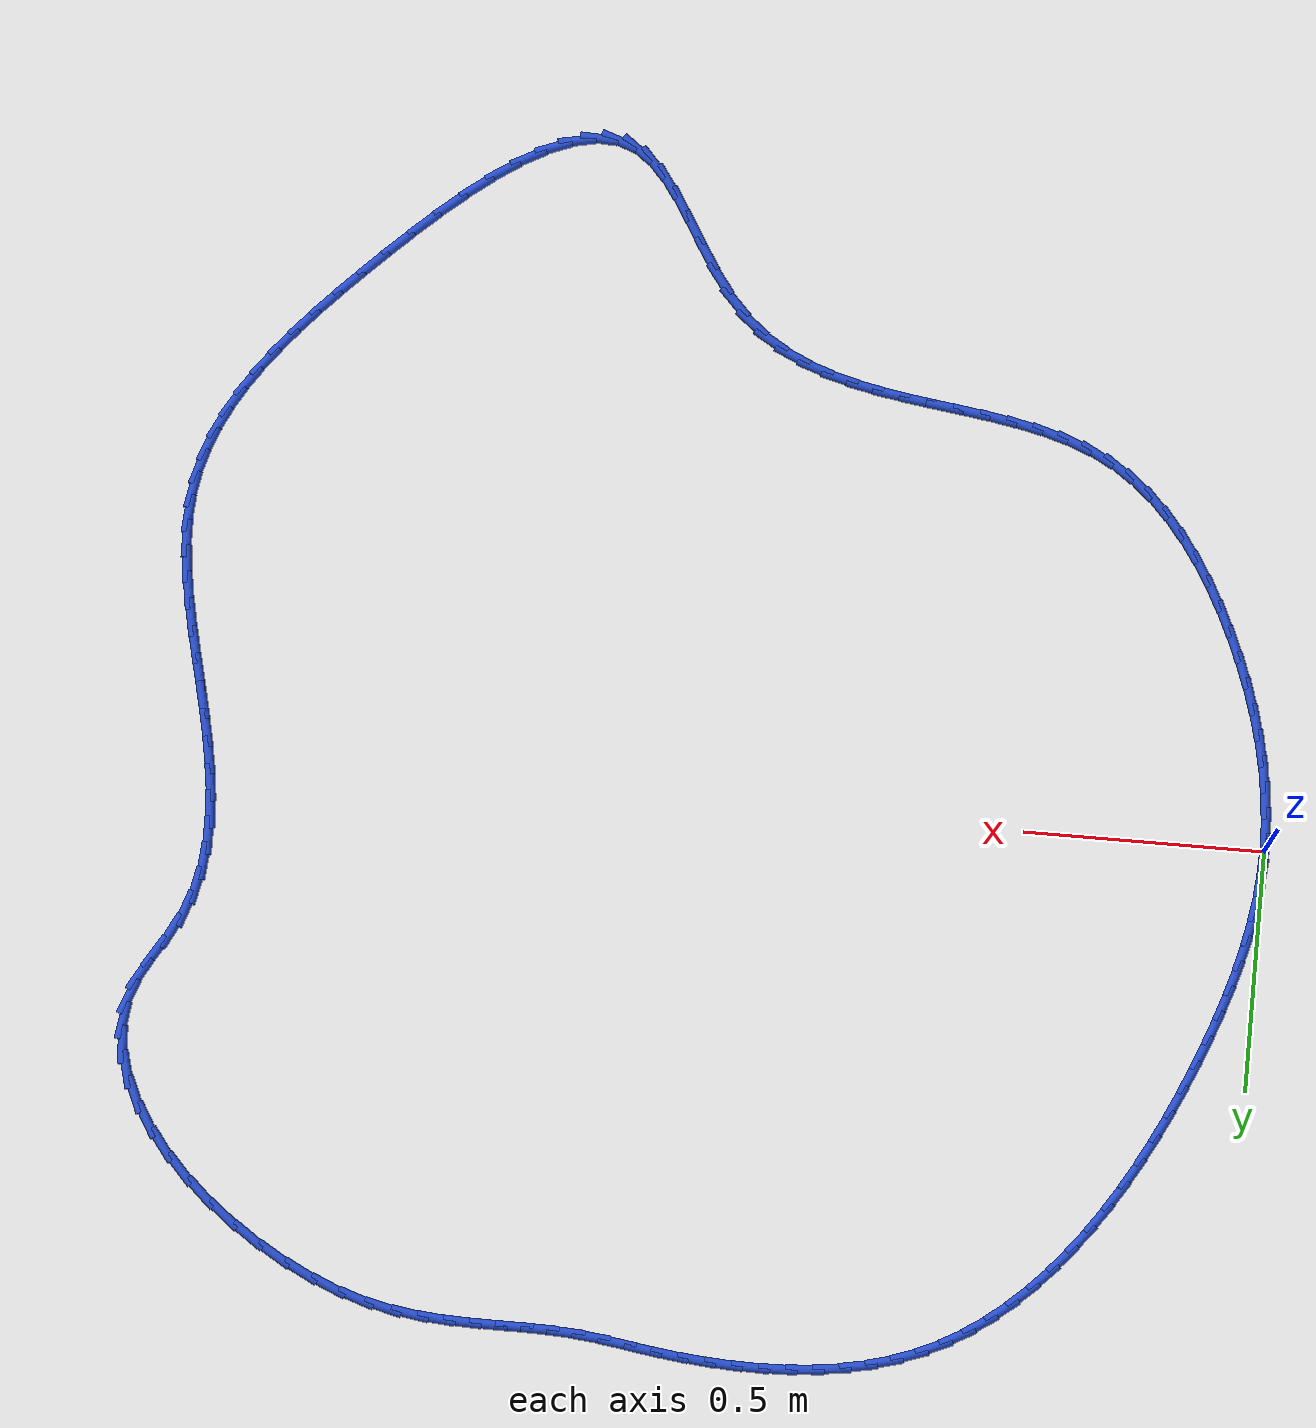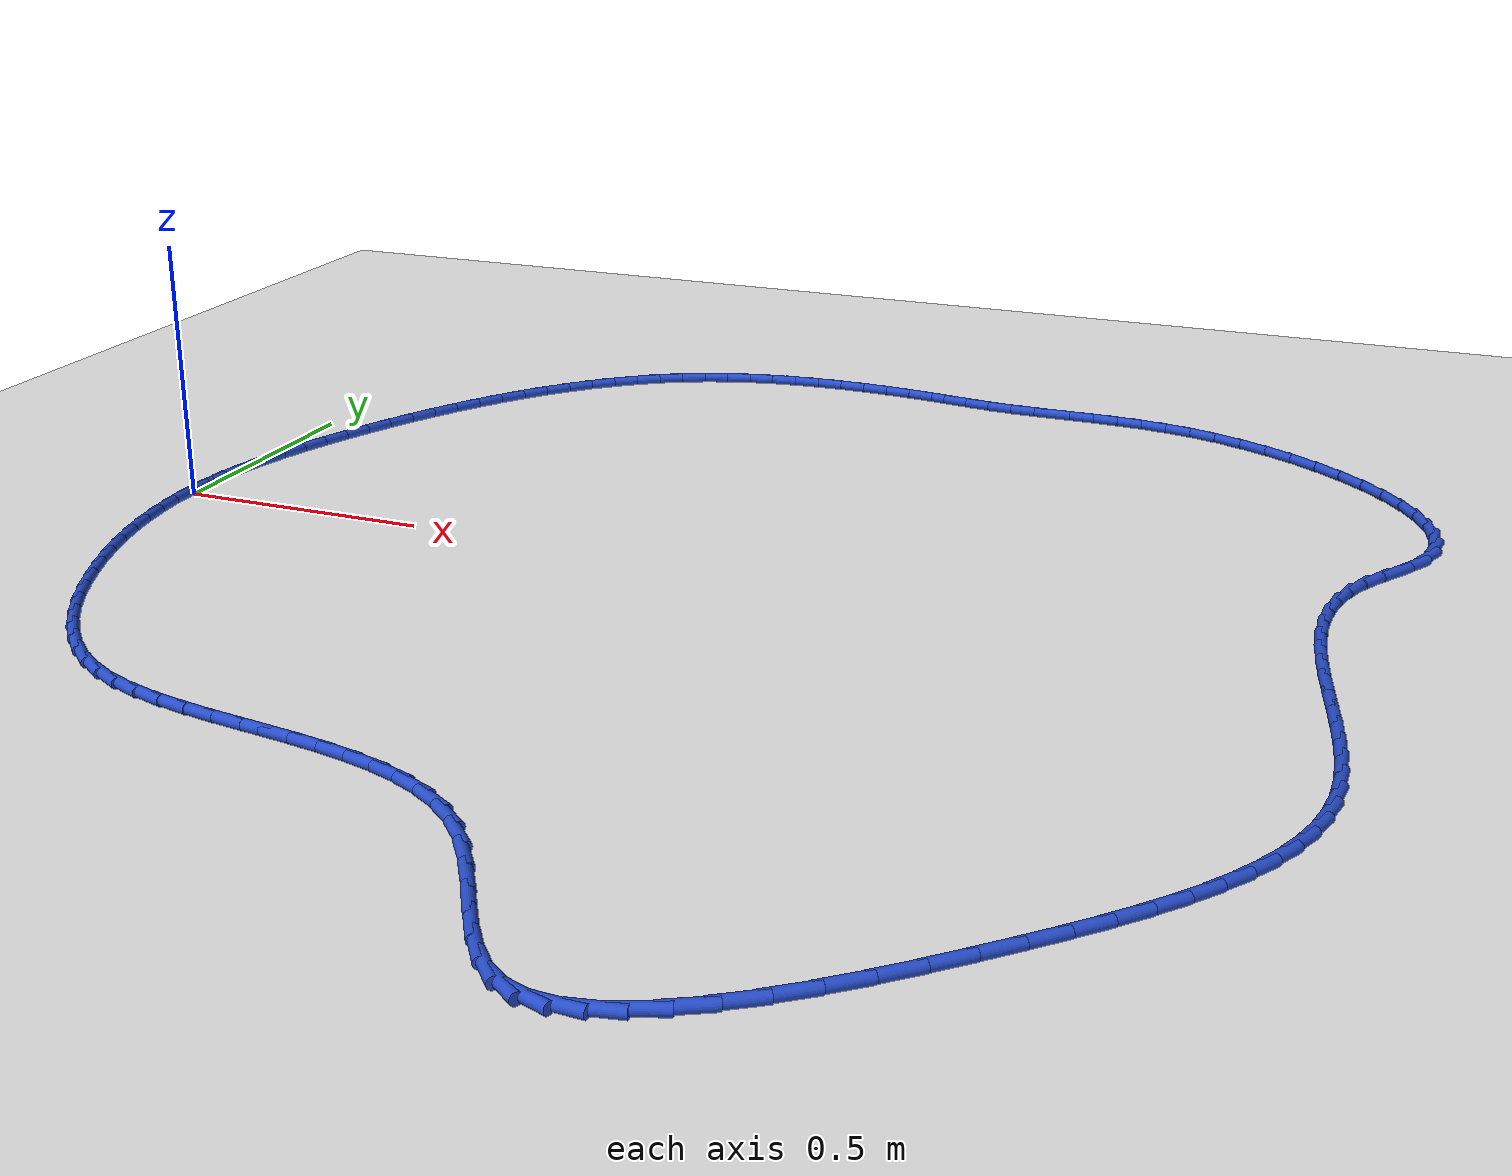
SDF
<sdf version="1.6">
 <world name="default">
  <light name="sun" type="directional">
   <pose>0 0 10 0 -0 0</pose>
   <diffuse>0.8 0.8 0.8 1</diffuse>
   <specular>0.2 0.2 0.2 1</specular>
   <attenuation>
    <range>1000</range>
    <constant>0.9</constant>
    <linear>0.01</linear>
    <quadratic>0.001</quadratic>
   </attenuation>
   <direction>-0.5 0.1 -0.9</direction>
  </light>
  <model name="ground_plane">
   <static>1</static>
   <link name="link">
    <collision name="collision">
     <geometry><plane><normal>0 0 1</normal><size>100 100</size></plane></geometry>
     <surface><friction><ode><mu>100</mu><mu2>50</mu2></ode></friction></surface>
    </collision>
    <visual name="visual">
     <cast_shadows>0</cast_shadows>
     <geometry><plane><normal>0 0 1</normal><size>100 100</size></plane></geometry>
     <material>
      <script><uri>file://media/materials/scripts/gazebo.material</uri><name>Gazebo/WhiteGlow</name></script>
     </material>
    </visual>
   </link>
  </model>
  <gravity>0 0 -9.8</gravity>
  <magnetic_field>6e-06 2.3e-05 -4.2e-05</magnetic_field>
  <atmosphere type="adiabatic"/>
  <physics name="default_physics" default="0" type="ode">
   <max_step_size>0.001</max_step_size>
   <real_time_factor>1</real_time_factor>
   <real_time_update_rate>1000</real_time_update_rate>
  </physics>
  <scene><ambient>0.4 0.4 0.4 1</ambient><background>0.7 0.7 0.7 1</background><shadows>1</shadows></scene>
  <spherical_coordinates>
   <surface_model>EARTH_WGS84</surface_model>
   <latitude_deg>0</latitude_deg>
   <longitude_deg>0</longitude_deg>
   <elevation>0</elevation>
   <heading_deg>0</heading_deg>
  </spherical_coordinates>
  <model name="line">
   <link name="link_0">
    <pose>2.2551405187698492e-17 8.326672684688674e-17 0.01 0 1.57 1.5280635900219666</pose>
    <collision name="collision">
     <geometry><cylinder><radius>0.01</radius><length>0.08</length></cylinder></geometry>
    </collision>
    <visual name="visual">
     <material>
      <script><name>Gazebo/Blue</name><uri>file://media/materials/scripts/gazebo.material</uri></script>
     </material>
     <geometry><cylinder><radius>0.01</radius><length>0.08</length></cylinder></geometry>
    </visual>
   </link>
   <link name="link_1">
    <pose>0.002290361997818722 0.05356473438542237 0.01 0 1.57 1.4670188387051344</pose>
    <collision name="collision">
     <geometry><cylinder><radius>0.01</radius><length>0.08</length></cylinder></geometry>
    </collision>
    <visual name="visual">
     <material>
      <script><name>Gazebo/Blue</name><uri>file://media/materials/scripts/gazebo.material</uri></script>
     </material>
     <geometry><cylinder><radius>0.01</radius><length>0.08</length></cylinder></geometry>
    </visual>
   </link>
   <link name="link_2">
    <pose>0.007856314260132209 0.1070055785124294 0.01 0 1.57 1.4110822218781334</pose>
    <collision name="collision">
     <geometry><cylinder><radius>0.01</radius><length>0.08</length></cylinder></geometry>
    </collision>
    <visual name="visual">
     <material>
      <script><name>Gazebo/Blue</name><uri>file://media/materials/scripts/gazebo.material</uri></script>
     </material>
     <geometry><cylinder><radius>0.01</radius><length>0.08</length></cylinder></geometry>
    </visual>
   </link>
   <link name="link_3">
    <pose>0.016448841105608347 0.1603467734238678 0.01 0 1.57 1.3604931127275217</pose>
    <collision name="collision">
     <geometry><cylinder><radius>0.01</radius><length>0.08</length></cylinder></geometry>
    </collision>
    <visual name="visual">
     <material>
      <script><name>Gazebo/Blue</name><uri>file://media/materials/scripts/gazebo.material</uri></script>
     </material>
     <geometry><cylinder><radius>0.01</radius><length>0.08</length></cylinder></geometry>
    </visual>
   </link>
   <link name="link_4">
    <pose>0.027818926852915017 0.2136125601625845 0.01 0 1.57 1.3153226943522283</pose>
    <collision name="collision">
     <geometry><cylinder><radius>0.01</radius><length>0.08</length></cylinder></geometry>
    </collision>
    <visual name="visual">
     <material>
      <script><name>Gazebo/Blue</name><uri>file://media/materials/scripts/gazebo.material</uri></script>
     </material>
     <geometry><cylinder><radius>0.01</radius><length>0.08</length></cylinder></geometry>
    </visual>
   </link>
   <link name="link_5">
    <pose>0.041717555820720106 0.2668271797714263 0.01 0 1.57 1.275517288848921</pose>
    <collision name="collision">
     <geometry><cylinder><radius>0.01</radius><length>0.08</length></cylinder></geometry>
    </collision>
    <visual name="visual">
     <material>
      <script><name>Gazebo/Blue</name><uri>file://media/materials/scripts/gazebo.material</uri></script>
     </material>
     <geometry><cylinder><radius>0.01</radius><length>0.08</length></cylinder></geometry>
    </visual>
   </link>
   <link name="link_6">
    <pose>0.05789571232769149 0.3200148732932398 0.01 0 1.57 1.2409397017827632</pose>
    <collision name="collision">
     <geometry><cylinder><radius>0.01</radius><length>0.08</length></cylinder></geometry>
    </collision>
    <visual name="visual">
     <material>
      <script><name>Gazebo/Blue</name><uri>file://media/materials/scripts/gazebo.material</uri></script>
     </material>
     <geometry><cylinder><radius>0.01</radius><length>0.08</length></cylinder></geometry>
    </visual>
   </link>
   <link name="link_7">
    <pose>0.076104380692497 0.3731998817708719 0.01 0 1.57 1.2114045515582856</pose>
    <collision name="collision">
     <geometry><cylinder><radius>0.01</radius><length>0.08</length></cylinder></geometry>
    </collision>
    <visual name="visual">
     <material>
      <script><name>Gazebo/Blue</name><uri>file://media/materials/scripts/gazebo.material</uri></script>
     </material>
     <geometry><cylinder><radius>0.01</radius><length>0.08</length></cylinder></geometry>
    </visual>
   </link>
   <link name="link_8">
    <pose>0.09609454523380462 0.42640644624716945 0.01 0 1.57 1.1860031495152337</pose>
    <collision name="collision">
     <geometry><cylinder><radius>0.01</radius><length>0.08</length></cylinder></geometry>
    </collision>
    <visual name="visual">
     <material>
      <script><name>Gazebo/Blue</name><uri>file://media/materials/scripts/gazebo.material</uri></script>
     </material>
     <geometry><cylinder><radius>0.01</radius><length>0.08</length></cylinder></geometry>
    </visual>
   </link>
   <link name="link_9">
    <pose>0.11764783165384408 0.4796268999807252 0.01 0 1.57 1.1602141189880262</pose>
    <collision name="collision">
     <geometry><cylinder><radius>0.01</radius><length>0.08</length></cylinder></geometry>
    </collision>
    <visual name="visual">
     <material>
      <script><name>Gazebo/Blue</name><uri>file://media/materials/scripts/gazebo.material</uri></script>
     </material>
     <geometry><cylinder><radius>0.01</radius><length>0.08</length></cylinder></geometry>
    </visual>
   </link>
   <link name="link_10">
    <pose>0.1407335693601218 0.5326581147778282 0.01 0 1.57 1.132166868489333</pose>
    <collision name="collision">
     <geometry><cylinder><radius>0.01</radius><length>0.08</length></cylinder></geometry>
    </collision>
    <visual name="visual">
     <material>
      <script><name>Gazebo/Blue</name><uri>file://media/materials/scripts/gazebo.material</uri></script>
     </material>
     <geometry><cylinder><radius>0.01</radius><length>0.08</length></cylinder></geometry>
    </visual>
   </link>
   <link name="link_11">
    <pose>0.16539213236818645 0.5852229815809066 0.01 0 1.57 1.101587255370738</pose>
    <collision name="collision">
     <geometry><cylinder><radius>0.01</radius><length>0.08</length></cylinder></geometry>
    </collision>
    <visual name="visual">
     <material>
      <script><name>Gazebo/Blue</name><uri>file://media/materials/scripts/gazebo.material</uri></script>
     </material>
     <geometry><cylinder><radius>0.01</radius><length>0.08</length></cylinder></geometry>
    </visual>
   </link>
   <link name="link_12">
    <pose>0.19166402845400904 0.6370442520436805 0.01 0 1.57 1.0681722411529264</pose>
    <collision name="collision">
     <geometry><cylinder><radius>0.01</radius><length>0.08</length></cylinder></geometry>
    </collision>
    <visual name="visual">
     <material>
      <script><name>Gazebo/Blue</name><uri>file://media/materials/scripts/gazebo.material</uri></script>
     </material>
     <geometry><cylinder><radius>0.01</radius><length>0.08</length></cylinder></geometry>
    </visual>
   </link>
   <link name="link_13">
    <pose>0.21958976539356062 0.6878446778198715 0.01 0 1.57 1.0315855189300964</pose>
    <collision name="collision">
     <geometry><cylinder><radius>0.01</radius><length>0.08</length></cylinder></geometry>
    </collision>
    <visual name="visual">
     <material>
      <script><name>Gazebo/Blue</name><uri>file://media/materials/scripts/gazebo.material</uri></script>
     </material>
     <geometry><cylinder><radius>0.01</radius><length>0.08</length></cylinder></geometry>
    </visual>
   </link>
   <link name="link_14">
    <pose>0.24920985096281206 0.7373470105631996 0.01 0 1.57 0.9914580876117127</pose>
    <collision name="collision">
     <geometry><cylinder><radius>0.01</radius><length>0.08</length></cylinder></geometry>
    </collision>
    <visual name="visual">
     <material>
      <script><name>Gazebo/Blue</name><uri>file://media/materials/scripts/gazebo.material</uri></script>
     </material>
     <geometry><cylinder><radius>0.01</radius><length>0.08</length></cylinder></geometry>
    </visual>
   </link>
   <link name="link_15">
    <pose>0.2805647929377344 0.7852740019273863 0.01 0 1.57 0.9473919513212403</pose>
    <collision name="collision">
     <geometry><cylinder><radius>0.01</radius><length>0.08</length></cylinder></geometry>
    </collision>
    <visual name="visual">
     <material>
      <script><name>Gazebo/Blue</name><uri>file://media/materials/scripts/gazebo.material</uri></script>
     </material>
     <geometry><cylinder><radius>0.01</radius><length>0.08</length></cylinder></geometry>
    </visual>
   </link>
   <link name="link_16">
    <pose>0.3136950990942987 0.8313484035661524 0.01 0 1.57 0.8989687052836557</pose>
    <collision name="collision">
     <geometry><cylinder><radius>0.01</radius><length>0.08</length></cylinder></geometry>
    </collision>
    <visual name="visual">
     <material>
      <script><name>Gazebo/Blue</name><uri>file://media/materials/scripts/gazebo.material</uri></script>
     </material>
     <geometry><cylinder><radius>0.01</radius><length>0.08</length></cylinder></geometry>
    </visual>
   </link>
   <link name="link_17">
    <pose>0.3486412772084759 0.8752929671332184 0.01 0 1.57 0.8457653338594834</pose>
    <collision name="collision">
     <geometry><cylinder><radius>0.01</radius><length>0.08</length></cylinder></geometry>
    </collision>
    <visual name="visual">
     <material>
      <script><name>Gazebo/Blue</name><uri>file://media/materials/scripts/gazebo.material</uri></script>
     </material>
     <geometry><cylinder><radius>0.01</radius><length>0.08</length></cylinder></geometry>
    </visual>
   </link>
   <link name="link_18">
    <pose>0.38544383505623697 0.9168304442823051 0.01 0 1.57 0.7873800034721977</pose>
    <collision name="collision">
     <geometry><cylinder><radius>0.01</radius><length>0.08</length></cylinder></geometry>
    </collision>
    <visual name="visual">
     <material>
      <script><name>Gazebo/Blue</name><uri>file://media/materials/scripts/gazebo.material</uri></script>
     </material>
     <geometry><cylinder><radius>0.01</radius><length>0.08</length></cylinder></geometry>
    </visual>
   </link>
   <link name="link_19">
    <pose>0.42414328041355287 0.9556835866671337 0.01 0 1.57 0.7234706470306219</pose>
    <collision name="collision">
     <geometry><cylinder><radius>0.01</radius><length>0.08</length></cylinder></geometry>
    </collision>
    <visual name="visual">
     <material>
      <script><name>Gazebo/Blue</name><uri>file://media/materials/scripts/gazebo.material</uri></script>
     </material>
     <geometry><cylinder><radius>0.01</radius><length>0.08</length></cylinder></geometry>
    </visual>
   </link>
   <link name="link_20">
    <pose>0.46478012105639477 0.9915751459414249 0.01 0 1.57 0.6538081331336639</pose>
    <collision name="collision">
     <geometry><cylinder><radius>0.01</radius><length>0.08</length></cylinder></geometry>
    </collision>
    <visual name="visual">
     <material>
      <script><name>Gazebo/Blue</name><uri>file://media/materials/scripts/gazebo.material</uri></script>
     </material>
     <geometry><cylinder><radius>0.01</radius><length>0.08</length></cylinder></geometry>
    </visual>
   </link>
   <link name="link_21">
    <pose>0.5073948647607336 1.0242278737588995 0.01 0 1.57 0.5783430279348372</pose>
    <collision name="collision">
     <geometry><cylinder><radius>0.01</radius><length>0.08</length></cylinder></geometry>
    </collision>
    <visual name="visual">
     <material>
      <script><name>Gazebo/Blue</name><uri>file://media/materials/scripts/gazebo.material</uri></script>
     </material>
     <geometry><cylinder><radius>0.01</radius><length>0.08</length></cylinder></geometry>
    </visual>
   </link>
   <link name="link_22">
    <pose>0.55202801930254 1.0533645217732777 0.01 0 1.57 0.4972797623357295</pose>
    <collision name="collision">
     <geometry><cylinder><radius>0.01</radius><length>0.08</length></cylinder></geometry>
    </collision>
    <visual name="visual">
     <material>
      <script><name>Gazebo/Blue</name><uri>file://media/materials/scripts/gazebo.material</uri></script>
     </material>
     <geometry><cylinder><radius>0.01</radius><length>0.08</length></cylinder></geometry>
    </visual>
   </link>
   <link name="link_23">
    <pose>0.5987200924577853 1.0787078416382814 0.01 0 1.57 0.4114415498475011</pose>
    <collision name="collision">
     <geometry><cylinder><radius>0.01</radius><length>0.08</length></cylinder></geometry>
    </collision>
    <visual name="visual">
     <material>
      <script><name>Gazebo/Blue</name><uri>file://media/materials/scripts/gazebo.material</uri></script>
     </material>
     <geometry><cylinder><radius>0.01</radius><length>0.08</length></cylinder></geometry>
    </visual>
   </link>
   <link name="link_24">
    <pose>0.6475032805815015 1.0999941977198155 0.01 0 1.57 0.32746401152332916</pose>
    <collision name="collision">
     <geometry><cylinder><radius>0.01</radius><length>0.08</length></cylinder></geometry>
    </collision>
    <visual name="visual">
     <material>
      <script><name>Gazebo/Blue</name><uri>file://media/materials/scripts/gazebo.material</uri></script>
     </material>
     <geometry><cylinder><radius>0.01</radius><length>0.08</length></cylinder></geometry>
    </visual>
   </link>
   <link name="link_25">
    <pose>0.6982444898250625 1.1172306719886038 0.01 0 1.57 0.2510609065994759</pose>
    <collision name="collision">
     <geometry><cylinder><radius>0.01</radius><length>0.08</length></cylinder></geometry>
    </collision>
    <visual name="visual">
     <material>
      <script><name>Gazebo/Blue</name><uri>file://media/materials/scripts/gazebo.material</uri></script>
     </material>
     <geometry><cylinder><radius>0.01</radius><length>0.08</length></cylinder></geometry>
    </visual>
   </link>
   <link name="link_26">
    <pose>0.7506585474194624 1.1306734261560811 0.01 0 1.57 0.1822522546144268</pose>
    <collision name="collision">
     <geometry><cylinder><radius>0.01</radius><length>0.08</length></cylinder></geometry>
    </collision>
    <visual name="visual">
     <material>
      <script><name>Gazebo/Blue</name><uri>file://media/materials/scripts/gazebo.material</uri></script>
     </material>
     <geometry><cylinder><radius>0.01</radius><length>0.08</length></cylinder></geometry>
    </visual>
   </link>
   <link name="link_27">
    <pose>0.8044546171806215 1.1405878976568014 0.01 0 1.57 0.12059901192361307</pose>
    <collision name="collision">
     <geometry><cylinder><radius>0.01</radius><length>0.08</length></cylinder></geometry>
    </collision>
    <visual name="visual">
     <material>
      <script><name>Gazebo/Blue</name><uri>file://media/materials/scripts/gazebo.material</uri></script>
     </material>
     <geometry><cylinder><radius>0.01</radius><length>0.08</length></cylinder></geometry>
    </visual>
   </link>
   <link name="link_28">
    <pose>0.8593418629244614 1.147239523925319 0.01 0 1.57 0.06552604040377356</pose>
    <collision name="collision">
     <geometry><cylinder><radius>0.01</radius><length>0.08</length></cylinder></geometry>
    </collision>
    <visual name="visual">
     <material>
      <script><name>Gazebo/Blue</name><uri>file://media/materials/scripts/gazebo.material</uri></script>
     </material>
     <geometry><cylinder><radius>0.01</radius><length>0.08</length></cylinder></geometry>
    </visual>
   </link>
   <link name="link_29">
    <pose>0.9150294484669029 1.1508937423961896 0.01 0 1.57 0.01640948564834614</pose>
    <collision name="collision">
     <geometry><cylinder><radius>0.01</radius><length>0.08</length></cylinder></geometry>
    </collision>
    <visual name="visual">
     <material>
      <script><name>Gazebo/Blue</name><uri>file://media/materials/scripts/gazebo.material</uri></script>
     </material>
     <geometry><cylinder><radius>0.01</radius><length>0.08</length></cylinder></geometry>
    </visual>
   </link>
   <link name="link_30">
    <pose>0.9712265376238666 1.1518159905039664 0.01 0 1.57 -0.02736645536917747</pose>
    <collision name="collision">
     <geometry><cylinder><radius>0.01</radius><length>0.08</length></cylinder></geometry>
    </collision>
    <visual name="visual">
     <material>
      <script><name>Gazebo/Blue</name><uri>file://media/materials/scripts/gazebo.material</uri></script>
     </material>
     <geometry><cylinder><radius>0.01</radius><length>0.08</length></cylinder></geometry>
    </visual>
   </link>
   <link name="link_31">
    <pose>1.0276422942112735 1.1502717056832044 0.01 0 1.57 -0.06637628809612008</pose>
    <collision name="collision">
     <geometry><cylinder><radius>0.01</radius><length>0.08</length></cylinder></geometry>
    </collision>
    <visual name="visual">
     <material>
      <script><name>Gazebo/Blue</name><uri>file://media/materials/scripts/gazebo.material</uri></script>
     </material>
     <geometry><cylinder><radius>0.01</radius><length>0.08</length></cylinder></geometry>
    </visual>
   </link>
   <link name="link_32">
    <pose>1.0839858820450448 1.1465263253684583 0.01 0 1.57 -0.10113606101652392</pose>
    <collision name="collision">
     <geometry><cylinder><radius>0.01</radius><length>0.08</length></cylinder></geometry>
    </collision>
    <visual name="visual">
     <material>
      <script><name>Gazebo/Blue</name><uri>file://media/materials/scripts/gazebo.material</uri></script>
     </material>
     <geometry><cylinder><radius>0.01</radius><length>0.08</length></cylinder></geometry>
    </visual>
   </link>
   <link name="link_33">
    <pose>1.1399664649411008 1.140845286994282 0.01 0 1.57 -0.13207742308611625</pose>
    <collision name="collision">
     <geometry><cylinder><radius>0.01</radius><length>0.08</length></cylinder></geometry>
    </collision>
    <visual name="visual">
     <material>
      <script><name>Gazebo/Blue</name><uri>file://media/materials/scripts/gazebo.material</uri></script>
     </material>
     <geometry><cylinder><radius>0.01</radius><length>0.08</length></cylinder></geometry>
    </visual>
   </link>
   <link name="link_34">
    <pose>1.1952935334830628 1.1334950402394344 0.01 0 1.57 -0.15188084753118042</pose>
    <collision name="collision">
     <geometry><cylinder><radius>0.01</radius><length>0.08</length></cylinder></geometry>
    </collision>
    <visual name="visual">
     <material>
      <script><name>Gazebo/Blue</name><uri>file://media/materials/scripts/gazebo.material</uri></script>
     </material>
     <geometry><cylinder><radius>0.01</radius><length>0.08</length></cylinder></geometry>
    </visual>
   </link>
   <link name="link_35">
    <pose>1.2498085945413606 1.125150988057739 0.01 0 1.57 -0.14065346948717775</pose>
    <collision name="collision">
     <geometry><cylinder><radius>0.01</radius><length>0.08</length></cylinder></geometry>
    </collision>
    <visual name="visual">
     <material>
      <script><name>Gazebo/Blue</name><uri>file://media/materials/scripts/gazebo.material</uri></script>
     </material>
     <geometry><cylinder><radius>0.01</radius><length>0.08</length></cylinder></geometry>
    </visual>
   </link>
   <link name="link_36">
    <pose>1.3036869164387312 1.1175224424934112 0.01 0 1.57 -0.09560418442787234</pose>
    <collision name="collision">
     <geometry><cylinder><radius>0.01</radius><length>0.08</length></cylinder></geometry>
    </collision>
    <visual name="visual">
     <material>
      <script><name>Gazebo/Blue</name><uri>file://media/materials/scripts/gazebo.material</uri></script>
     </material>
     <geometry><cylinder><radius>0.01</radius><length>0.08</length></cylinder></geometry>
    </visual>
   </link>
   <link name="link_37">
    <pose>1.3571548655604277 1.1123950515726995 0.01 0 1.57 -0.044473799728148286</pose>
    <collision name="collision">
     <geometry><cylinder><radius>0.01</radius><length>0.08</length></cylinder></geometry>
    </collision>
    <visual name="visual">
     <material>
      <script><name>Gazebo/Blue</name><uri>file://media/materials/scripts/gazebo.material</uri></script>
     </material>
     <geometry><cylinder><radius>0.01</radius><length>0.08</length></cylinder></geometry>
    </visual>
   </link>
   <link name="link_38">
    <pose>1.4104235965559766 1.1100244255238378 0.01 0 1.57 -0.012918150865808532</pose>
    <collision name="collision">
     <geometry><cylinder><radius>0.01</radius><length>0.08</length></cylinder></geometry>
    </collision>
    <visual name="visual">
     <material>
      <script><name>Gazebo/Blue</name><uri>file://media/materials/scripts/gazebo.material</uri></script>
     </material>
     <geometry><cylinder><radius>0.01</radius><length>0.08</length></cylinder></geometry>
    </visual>
   </link>
   <link name="link_39">
    <pose>1.4636910420801956 1.1093362703464313 0.01 0 1.57 -0.0023242293383107107</pose>
    <collision name="collision">
     <geometry><cylinder><radius>0.01</radius><length>0.08</length></cylinder></geometry>
    </collision>
    <visual name="visual">
     <material>
      <script><name>Gazebo/Blue</name><uri>file://media/materials/scripts/gazebo.material</uri></script>
     </material>
     <geometry><cylinder><radius>0.01</radius><length>0.08</length></cylinder></geometry>
    </visual>
   </link>
   <link name="link_40">
    <pose>1.5171546945163963 1.1092120083331496 0.01 0 1.57 -0.012605718101820682</pose>
    <collision name="collision">
     <geometry><cylinder><radius>0.01</radius><length>0.08</length></cylinder></geometry>
    </collision>
    <visual name="visual">
     <material>
      <script><name>Gazebo/Blue</name><uri>file://media/materials/scripts/gazebo.material</uri></script>
     </material>
     <geometry><cylinder><radius>0.01</radius><length>0.08</length></cylinder></geometry>
    </visual>
   </link>
   <link name="link_41">
    <pose>1.571012046247889 1.1085330617766604 0.01 0 1.57 -0.043173737893640346</pose>
    <collision name="collision">
     <geometry><cylinder><radius>0.01</radius><length>0.08</length></cylinder></geometry>
    </collision>
    <visual name="visual">
     <material>
      <script><name>Gazebo/Blue</name><uri>file://media/materials/scripts/gazebo.material</uri></script>
     </material>
     <geometry><cylinder><radius>0.01</radius><length>0.08</length></cylinder></geometry>
    </visual>
   </link>
   <link name="link_42">
    <pose>1.6254605896579868 1.1061808529696338 0.01 0 1.57 -0.0928586615179386</pose>
    <collision name="collision">
     <geometry><cylinder><radius>0.01</radius><length>0.08</length></cylinder></geometry>
    </collision>
    <visual name="visual">
     <material>
      <script><name>Gazebo/Blue</name><uri>file://media/materials/scripts/gazebo.material</uri></script>
     </material>
     <geometry><cylinder><radius>0.01</radius><length>0.08</length></cylinder></geometry>
    </visual>
   </link>
   <link name="link_43">
    <pose>1.6806978171299982 1.1010368042047372 0.01 0 1.57 -0.1596734627402512</pose>
    <collision name="collision">
     <geometry><cylinder><radius>0.01</radius><length>0.08</length></cylinder></geometry>
    </collision>
    <visual name="visual">
     <material>
      <script><name>Gazebo/Blue</name><uri>file://media/materials/scripts/gazebo.material</uri></script>
     </material>
     <geometry><cylinder><radius>0.01</radius><length>0.08</length></cylinder></geometry>
    </visual>
   </link>
   <link name="link_44">
    <pose>1.7369212210472371 1.0919823377746407 0.01 0 1.57 -0.24056703282645728</pose>
    <collision name="collision">
     <geometry><cylinder><radius>0.01</radius><length>0.08</length></cylinder></geometry>
    </collision>
    <visual name="visual">
     <material>
      <script><name>Gazebo/Blue</name><uri>file://media/materials/scripts/gazebo.material</uri></script>
     </material>
     <geometry><cylinder><radius>0.01</radius><length>0.08</length></cylinder></geometry>
    </visual>
   </link>
   <link name="link_45">
    <pose>1.7943279041669606 1.0778994579160637 0.01 0 1.57 -0.32682078058079633</pose>
    <collision name="collision">
     <geometry><cylinder><radius>0.01</radius><length>0.08</length></cylinder></geometry>
    </collision>
    <visual name="visual">
     <material>
      <script><name>Gazebo/Blue</name><uri>file://media/materials/scripts/gazebo.material</uri></script>
     </material>
     <geometry><cylinder><radius>0.01</radius><length>0.08</length></cylinder></geometry>
    </visual>
   </link>
   <link name="link_46">
    <pose>1.8528535366499002 1.0580606436388436 0.01 0 1.57 -0.40527572523311445</pose>
    <collision name="collision">
     <geometry><cylinder><radius>0.01</radius><length>0.08</length></cylinder></geometry>
    </collision>
    <visual name="visual">
     <material>
      <script><name>Gazebo/Blue</name><uri>file://media/materials/scripts/gazebo.material</uri></script>
     </material>
     <geometry><cylinder><radius>0.01</radius><length>0.08</length></cylinder></geometry>
    </visual>
   </link>
   <link name="link_47">
    <pose>1.911719139091342 1.0328057719384887 0.01 0 1.57 -0.47724063288800106</pose>
    <collision name="collision">
     <geometry><cylinder><radius>0.01</radius><length>0.08</length></cylinder></geometry>
    </collision>
    <visual name="visual">
     <material>
      <script><name>Gazebo/Blue</name><uri>file://media/materials/scripts/gazebo.material</uri></script>
     </material>
     <geometry><cylinder><radius>0.01</radius><length>0.08</length></cylinder></geometry>
    </visual>
   </link>
   <link name="link_48">
    <pose>1.9700247293467827 1.0026554490615425 0.01 0 1.57 -0.5458063292827189</pose>
    <collision name="collision">
     <geometry><cylinder><radius>0.01</radius><length>0.08</length></cylinder></geometry>
    </collision>
    <visual name="visual">
     <material>
      <script><name>Gazebo/Blue</name><uri>file://media/materials/scripts/gazebo.material</uri></script>
     </material>
     <geometry><cylinder><radius>0.01</radius><length>0.08</length></cylinder></geometry>
    </visual>
   </link>
   <link name="link_49">
    <pose>2.0268703252717164 0.9681302812545499 0.01 0 1.57 -0.613669647728787</pose>
    <collision name="collision">
     <geometry><cylinder><radius>0.01</radius><length>0.08</length></cylinder></geometry>
    </collision>
    <visual name="visual">
     <material>
      <script><name>Gazebo/Blue</name><uri>file://media/materials/scripts/gazebo.material</uri></script>
     </material>
     <geometry><cylinder><radius>0.01</radius><length>0.08</length></cylinder></geometry>
    </visual>
   </link>
   <link name="link_50">
    <pose>2.0813559447216394 0.9297508747640546 0.01 0 1.57 -0.6833996395674194</pose>
    <collision name="collision">
     <geometry><cylinder><radius>0.01</radius><length>0.08</length></cylinder></geometry>
    </collision>
    <visual name="visual">
     <material>
      <script><name>Gazebo/Blue</name><uri>file://media/materials/scripts/gazebo.material</uri></script>
     </material>
     <geometry><cylinder><radius>0.01</radius><length>0.08</length></cylinder></geometry>
    </visual>
   </link>
   <link name="link_51">
    <pose>2.1325816055520463 0.8880378358366012 0.01 0 1.57 -0.7576772888659113</pose>
    <collision name="collision">
     <geometry><cylinder><radius>0.01</radius><length>0.08</length></cylinder></geometry>
    </collision>
    <visual name="visual">
     <material>
      <script><name>Gazebo/Blue</name><uri>file://media/materials/scripts/gazebo.material</uri></script>
     </material>
     <geometry><cylinder><radius>0.01</radius><length>0.08</length></cylinder></geometry>
    </visual>
   </link>
   <link name="link_52">
    <pose>2.179647325618433 0.8435117707187334 0.01 0 1.57 -0.8395273555790623</pose>
    <collision name="collision">
     <geometry><cylinder><radius>0.01</radius><length>0.08</length></cylinder></geometry>
    </collision>
    <visual name="visual">
     <material>
      <script><name>Gazebo/Blue</name><uri>file://media/materials/scripts/gazebo.material</uri></script>
     </material>
     <geometry><cylinder><radius>0.01</radius><length>0.08</length></cylinder></geometry>
    </visual>
   </link>
   <link name="link_53">
    <pose>2.2216531227762943 0.7966932856569958 0.01 0 1.57 -0.9325425542378575</pose>
    <collision name="collision">
     <geometry><cylinder><radius>0.01</radius><length>0.08</length></cylinder></geometry>
    </collision>
    <visual name="visual">
     <material>
      <script><name>Gazebo/Blue</name><uri>file://media/materials/scripts/gazebo.material</uri></script>
     </material>
     <geometry><cylinder><radius>0.01</radius><length>0.08</length></cylinder></geometry>
    </visual>
   </link>
   <link name="link_54">
    <pose>2.257699014881125 0.7481029868979323 0.01 0 1.57 -1.041050001515718</pose>
    <collision name="collision">
     <geometry><cylinder><radius>0.01</radius><length>0.08</length></cylinder></geometry>
    </collision>
    <visual name="visual">
     <material>
      <script><name>Gazebo/Blue</name><uri>file://media/materials/scripts/gazebo.material</uri></script>
     </material>
     <geometry><cylinder><radius>0.01</radius><length>0.08</length></cylinder></geometry>
    </visual>
   </link>
   <link name="link_55">
    <pose>2.2868850197884214 0.6982614806880869 0.01 0 1.57 -1.1700485356183823</pose>
    <collision name="collision">
     <geometry><cylinder><radius>0.01</radius><length>0.08</length></cylinder></geometry>
    </collision>
    <visual name="visual">
     <material>
      <script><name>Gazebo/Blue</name><uri>file://media/materials/scripts/gazebo.material</uri></script>
     </material>
     <geometry><cylinder><radius>0.01</radius><length>0.08</length></cylinder></geometry>
    </visual>
   </link>
   <link name="link_56">
    <pose>2.3083111553536777 0.6476893732740043 0.01 0 1.57 -1.324506682947514</pose>
    <collision name="collision">
     <geometry><cylinder><radius>0.01</radius><length>0.08</length></cylinder></geometry>
    </collision>
    <visual name="visual">
     <material>
      <script><name>Gazebo/Blue</name><uri>file://media/materials/scripts/gazebo.material</uri></script>
     </material>
     <geometry><cylinder><radius>0.01</radius><length>0.08</length></cylinder></geometry>
    </visual>
   </link>
   <link name="link_57">
    <pose>2.3210774394323903 0.5969072709022283 0.01 0 1.57 -1.507351657443786</pose>
    <collision name="collision">
     <geometry><cylinder><radius>0.01</radius><length>0.08</length></cylinder></geometry>
    </collision>
    <visual name="visual">
     <material>
      <script><name>Gazebo/Blue</name><uri>file://media/materials/scripts/gazebo.material</uri></script>
     </material>
     <geometry><cylinder><radius>0.01</radius><length>0.08</length></cylinder></geometry>
    </visual>
   </link>
   <link name="link_58">
    <pose>2.3242838898800535 0.5464357798193034 0.01 0 1.57 1.4257045521965226</pose>
    <collision name="collision">
     <geometry><cylinder><radius>0.01</radius><length>0.08</length></cylinder></geometry>
    </collision>
    <visual name="visual">
     <material>
      <script><name>Gazebo/Blue</name><uri>file://media/materials/scripts/gazebo.material</uri></script>
     </material>
     <geometry><cylinder><radius>0.01</radius><length>0.08</length></cylinder></geometry>
    </visual>
   </link>
   <link name="link_59">
    <pose>2.317030524552163 0.49679550627177327 0.01 0 1.57 1.2051560144287368</pose>
    <collision name="collision">
     <geometry><cylinder><radius>0.01</radius><length>0.08</length></cylinder></geometry>
    </collision>
    <visual name="visual">
     <material>
      <script><name>Gazebo/Blue</name><uri>file://media/materials/scripts/gazebo.material</uri></script>
     </material>
     <geometry><cylinder><radius>0.01</radius><length>0.08</length></cylinder></geometry>
    </visual>
   </link>
   <link name="link_60">
    <pose>2.2985329453777528 0.4484807955326286 0.01 0 1.57 1.0495894341357448</pose>
    <collision name="collision">
     <geometry><cylinder><radius>0.01</radius><length>0.08</length></cylinder></geometry>
    </collision>
    <visual name="visual">
     <material>
      <script><name>Gazebo/Blue</name><uri>file://media/materials/scripts/gazebo.material</uri></script>
     </material>
     <geometry><cylinder><radius>0.01</radius><length>0.08</length></cylinder></geometry>
    </visual>
   </link>
   <link name="link_61">
    <pose>2.2713952051657813 0.4012161288596668 0.01 0 1.57 1.016477158710644</pose>
    <collision name="collision">
     <geometry><cylinder><radius>0.01</radius><length>0.08</length></cylinder></geometry>
    </collision>
    <visual name="visual">
     <material>
      <script><name>Gazebo/Blue</name><uri>file://media/materials/scripts/gazebo.material</uri></script>
     </material>
     <geometry><cylinder><radius>0.01</radius><length>0.08</length></cylinder></geometry>
    </visual>
   </link>
   <link name="link_62">
    <pose>2.242073086862117 0.35385086535790333 0.01 0 1.57 1.0965608662463282</pose>
    <collision name="collision">
     <geometry><cylinder><radius>0.01</radius><length>0.08</length></cylinder></geometry>
    </collision>
    <visual name="visual">
     <material>
      <script><name>Gazebo/Blue</name><uri>file://media/materials/scripts/gazebo.material</uri></script>
     </material>
     <geometry><cylinder><radius>0.01</radius><length>0.08</length></cylinder></geometry>
    </visual>
   </link>
   <link name="link_63">
    <pose>2.2171058104328525 0.3052107003763693 0.01 0 1.57 1.2367962862194088</pose>
    <collision name="collision">
     <geometry><cylinder><radius>0.01</radius><length>0.08</length></cylinder></geometry>
    </collision>
    <visual name="visual">
     <material>
      <script><name>Gazebo/Blue</name><uri>file://media/materials/scripts/gazebo.material</uri></script>
     </material>
     <geometry><cylinder><radius>0.01</radius><length>0.08</length></cylinder></geometry>
    </visual>
   </link>
   <link name="link_64">
    <pose>2.1996034289293935 0.25477161318875824 0.01 0 1.57 1.3681958739009086</pose>
    <collision name="collision">
     <geometry><cylinder><radius>0.01</radius><length>0.08</length></cylinder></geometry>
    </collision>
    <visual name="visual">
     <material>
      <script><name>Gazebo/Blue</name><uri>file://media/materials/scripts/gazebo.material</uri></script>
     </material>
     <geometry><cylinder><radius>0.01</radius><length>0.08</length></cylinder></geometry>
    </visual>
   </link>
   <link name="link_65">
    <pose>2.1889117503856212 0.20272340892917723 0.01 0 1.57 1.482544848705377</pose>
    <collision name="collision">
     <geometry><cylinder><radius>0.01</radius><length>0.08</length></cylinder></geometry>
    </collision>
    <visual name="visual">
     <material>
      <script><name>Gazebo/Blue</name><uri>file://media/materials/scripts/gazebo.material</uri></script>
     </material>
     <geometry><cylinder><radius>0.01</radius><length>0.08</length></cylinder></geometry>
    </visual>
   </link>
   <link name="link_66">
    <pose>2.1841841044011403 0.14929239303480019 0.01 0 1.57 -1.5636571576500735</pose>
    <collision name="collision">
     <geometry><cylinder><radius>0.01</radius><length>0.08</length></cylinder></geometry>
    </collision>
    <visual name="visual">
     <material>
      <script><name>Gazebo/Blue</name><uri>file://media/materials/scripts/gazebo.material</uri></script>
     </material>
     <geometry><cylinder><radius>0.01</radius><length>0.08</length></cylinder></geometry>
    </visual>
   </link>
   <link name="link_67">
    <pose>2.184573820575558 0.09470487094280211 0.01 0 1.57 -1.48704816596049</pose>
    <collision name="collision">
     <geometry><cylinder><radius>0.01</radius><length>0.08</length></cylinder></geometry>
    </collision>
    <visual name="visual">
     <material>
      <script><name>Gazebo/Blue</name><uri>file://media/materials/scripts/gazebo.material</uri></script>
     </material>
     <geometry><cylinder><radius>0.01</radius><length>0.08</length></cylinder></geometry>
    </visual>
   </link>
   <link name="link_68">
    <pose>2.189234228508481 0.039187148090356595 0.01 0 1.57 -1.4279795663344435</pose>
    <collision name="collision">
     <geometry><cylinder><radius>0.01</radius><length>0.08</length></cylinder></geometry>
    </collision>
    <visual name="visual">
     <material>
      <script><name>Gazebo/Blue</name><uri>file://media/materials/scripts/gazebo.material</uri></script>
     </material>
     <geometry><cylinder><radius>0.01</radius><length>0.08</length></cylinder></geometry>
    </visual>
   </link>
   <link name="link_69">
    <pose>2.1973186577995145 -0.017034470085361225 0.01 0 1.57 -1.3849257255704295</pose>
    <collision name="collision">
     <geometry><cylinder><radius>0.01</radius><length>0.08</length></cylinder></geometry>
    </collision>
    <visual name="visual">
     <material>
      <script><name>Gazebo/Blue</name><uri>file://media/materials/scripts/gazebo.material</uri></script>
     </material>
     <geometry><cylinder><radius>0.01</radius><length>0.08</length></cylinder></geometry>
    </visual>
   </link>
   <link name="link_70">
    <pose>2.2079804380482653 -0.07373367814717799 0.01 0 1.57 -1.356535809975554</pose>
    <collision name="collision">
     <geometry><cylinder><radius>0.01</radius><length>0.08</length></cylinder></geometry>
    </collision>
    <visual name="visual">
     <material>
      <script><name>Gazebo/Blue</name><uri>file://media/materials/scripts/gazebo.material</uri></script>
     </material>
     <geometry><cylinder><radius>0.01</radius><length>0.08</length></cylinder></geometry>
    </visual>
   </link>
   <link name="link_71">
    <pose>2.2203728988543388 -0.1306841706579184 0.01 0 1.57 -1.341860793427429</pose>
    <collision name="collision">
     <geometry><cylinder><radius>0.01</radius><length>0.08</length></cylinder></geometry>
    </collision>
    <visual name="visual">
     <material>
      <script><name>Gazebo/Blue</name><uri>file://media/materials/scripts/gazebo.material</uri></script>
     </material>
     <geometry><cylinder><radius>0.01</radius><length>0.08</length></cylinder></geometry>
    </visual>
   </link>
   <link name="link_72">
    <pose>2.2336493698173423 -0.1876596421804087 0.01 0 1.57 -1.3404536822452415</pose>
    <collision name="collision">
     <geometry><cylinder><radius>0.01</radius><length>0.08</length></cylinder></geometry>
    </collision>
    <visual name="visual">
     <material>
      <script><name>Gazebo/Blue</name><uri>file://media/materials/scripts/gazebo.material</uri></script>
     </material>
     <geometry><cylinder><radius>0.01</radius><length>0.08</length></cylinder></geometry>
    </visual>
   </link>
   <link name="link_73">
    <pose>2.2469631805368815 -0.24443378727747544 0.01 0 1.57 -1.3524143530486437</pose>
    <collision name="collision">
     <geometry><cylinder><radius>0.01</radius><length>0.08</length></cylinder></geometry>
    </collision>
    <visual name="visual">
     <material>
      <script><name>Gazebo/Blue</name><uri>file://media/materials/scripts/gazebo.material</uri></script>
     </material>
     <geometry><cylinder><radius>0.01</radius><length>0.08</length></cylinder></geometry>
    </visual>
   </link>
   <link name="link_74">
    <pose>2.2594676606125614 -0.3007803005119425 0.01 0 1.57 -1.3784132512068</pose>
    <collision name="collision">
     <geometry><cylinder><radius>0.01</radius><length>0.08</length></cylinder></geometry>
    </collision>
    <visual name="visual">
     <material>
      <script><name>Gazebo/Blue</name><uri>file://media/materials/scripts/gazebo.material</uri></script>
     </material>
     <geometry><cylinder><radius>0.01</radius><length>0.08</length></cylinder></geometry>
    </visual>
   </link>
   <link name="link_75">
    <pose>2.270316139643991 -0.35647287644663667 0.01 0 1.57 -1.419695389007235</pose>
    <collision name="collision">
     <geometry><cylinder><radius>0.01</radius><length>0.08</length></cylinder></geometry>
    </collision>
    <visual name="visual">
     <material>
      <script><name>Gazebo/Blue</name><uri>file://media/materials/scripts/gazebo.material</uri></script>
     </material>
     <geometry><cylinder><radius>0.01</radius><length>0.08</length></cylinder></geometry>
    </visual>
   </link>
   <link name="link_76">
    <pose>2.278661947230774 -0.4112852096443834 0.01 0 1.57 -1.4780293225254646</pose>
    <collision name="collision">
     <geometry><cylinder><radius>0.01</radius><length>0.08</length></cylinder></geometry>
    </collision>
    <visual name="visual">
     <material>
      <script><name>Gazebo/Blue</name><uri>file://media/materials/scripts/gazebo.material</uri></script>
     </material>
     <geometry><cylinder><radius>0.01</radius><length>0.08</length></cylinder></geometry>
    </visual>
   </link>
   <link name="link_77">
    <pose>2.283658412972516 -0.46499099466800853 0.01 0 1.57 -1.5555137913919852</pose>
    <collision name="collision">
     <geometry><cylinder><radius>0.01</radius><length>0.08</length></cylinder></geometry>
    </collision>
    <visual name="visual">
     <material>
      <script><name>Gazebo/Blue</name><uri>file://media/materials/scripts/gazebo.material</uri></script>
     </material>
     <geometry><cylinder><radius>0.01</radius><length>0.08</length></cylinder></geometry>
    </visual>
   </link>
   <link name="link_78">
    <pose>2.2844588664688255 -0.5173639260803384 0.01 0 1.57 1.4879993568313852</pose>
    <collision name="collision">
     <geometry><cylinder><radius>0.01</radius><length>0.08</length></cylinder></geometry>
    </collision>
    <visual name="visual">
     <material>
      <script><name>Gazebo/Blue</name><uri>file://media/materials/scripts/gazebo.material</uri></script>
     </material>
     <geometry><cylinder><radius>0.01</radius><length>0.08</length></cylinder></geometry>
    </visual>
   </link>
   <link name="link_79">
    <pose>2.280241203972976 -0.5681872865945572 0.01 0 1.57 1.3801848130407448</pose>
    <collision name="collision">
     <geometry><cylinder><radius>0.01</radius><length>0.08</length></cylinder></geometry>
    </collision>
    <visual name="visual">
     <material>
      <script><name>Gazebo/Blue</name><uri>file://media/materials/scripts/gazebo.material</uri></script>
     </material>
     <geometry><cylinder><radius>0.01</radius><length>0.08</length></cylinder></geometry>
    </visual>
   </link>
   <link name="link_80">
    <pose>2.270733974750749 -0.6174592739851961 0.01 0 1.57 1.2765421704639537</pose>
    <collision name="collision">
     <geometry><cylinder><radius>0.01</radius><length>0.08</length></cylinder></geometry>
    </collision>
    <visual name="visual">
     <material>
      <script><name>Gazebo/Blue</name><uri>file://media/materials/scripts/gazebo.material</uri></script>
     </material>
     <geometry><cylinder><radius>0.01</radius><length>0.08</length></cylinder></geometry>
    </visual>
   </link>
   <link name="link_81">
    <pose>2.2562085087130908 -0.6653899285719131 0.01 0 1.57 1.1806394506742548</pose>
    <collision name="collision">
     <geometry><cylinder><radius>0.01</radius><length>0.08</length></cylinder></geometry>
    </collision>
    <visual name="visual">
     <material>
      <script><name>Gazebo/Blue</name><uri>file://media/materials/scripts/gazebo.material</uri></script>
     </material>
     <geometry><cylinder><radius>0.01</radius><length>0.08</length></cylinder></geometry>
    </visual>
   </link>
   <link name="link_82">
    <pose>2.236959127848804 -0.7121982642815408 0.01 0 1.57 1.0945688222387244</pose>
    <collision name="collision">
     <geometry><cylinder><radius>0.01</radius><length>0.08</length></cylinder></geometry>
    </collision>
    <visual name="visual">
     <material>
      <script><name>Gazebo/Blue</name><uri>file://media/materials/scripts/gazebo.material</uri></script>
     </material>
     <geometry><cylinder><radius>0.01</radius><length>0.08</length></cylinder></geometry>
    </visual>
   </link>
   <link name="link_83">
    <pose>2.2132801541466915 -0.7581032950409091 0.01 0 1.57 1.0193643728738007</pose>
    <collision name="collision">
     <geometry><cylinder><radius>0.01</radius><length>0.08</length></cylinder></geometry>
    </collision>
    <visual name="visual">
     <material>
      <script><name>Gazebo/Blue</name><uri>file://media/materials/scripts/gazebo.material</uri></script>
     </material>
     <geometry><cylinder><radius>0.01</radius><length>0.08</length></cylinder></geometry>
    </visual>
   </link>
   <link name="link_84">
    <pose>2.185465909595557 -0.8033240347768503 0.01 0 1.57 0.9551929601029895</pose>
    <collision name="collision">
     <geometry><cylinder><radius>0.01</radius><length>0.08</length></cylinder></geometry>
    </collision>
    <visual name="visual">
     <material>
      <script><name>Gazebo/Blue</name><uri>file://media/materials/scripts/gazebo.material</uri></script>
     </material>
     <geometry><cylinder><radius>0.01</radius><length>0.08</length></cylinder></geometry>
    </visual>
   </link>
   <link name="link_85">
    <pose>2.1538107161842017 -0.8480794974161961 0.01 0 1.57 0.9016358362586027</pose>
    <collision name="collision">
     <geometry><cylinder><radius>0.01</radius><length>0.08</length></cylinder></geometry>
    </collision>
    <visual name="visual">
     <material>
      <script><name>Gazebo/Blue</name><uri>file://media/materials/scripts/gazebo.material</uri></script>
     </material>
     <geometry><cylinder><radius>0.01</radius><length>0.08</length></cylinder></geometry>
    </visual>
   </link>
   <link name="link_86">
    <pose>2.1186088959014295 -0.8925886968857779 0.01 0 1.57 0.8579509660002833</pose>
    <collision name="collision">
     <geometry><cylinder><radius>0.01</radius><length>0.08</length></cylinder></geometry>
    </collision>
    <visual name="visual">
     <material>
      <script><name>Gazebo/Blue</name><uri>file://media/materials/scripts/gazebo.material</uri></script>
     </material>
     <geometry><cylinder><radius>0.01</radius><length>0.08</length></cylinder></geometry>
    </visual>
   </link>
   <link name="link_87">
    <pose>2.080154770736042 -0.9370706471124275 0.01 0 1.57 0.8232679009975615</pose>
    <collision name="collision">
     <geometry><cylinder><radius>0.01</radius><length>0.08</length></cylinder></geometry>
    </collision>
    <visual name="visual">
     <material>
      <script><name>Gazebo/Blue</name><uri>file://media/materials/scripts/gazebo.material</uri></script>
     </material>
     <geometry><cylinder><radius>0.01</radius><length>0.08</length></cylinder></geometry>
    </visual>
   </link>
   <link name="link_88">
    <pose>2.0387426626768432 -0.9817443620229758 0.01 0 1.57 0.7967112920725055</pose>
    <collision name="collision">
     <geometry><cylinder><radius>0.01</radius><length>0.08</length></cylinder></geometry>
    </collision>
    <visual name="visual">
     <material>
      <script><name>Gazebo/Blue</name><uri>file://media/materials/scripts/gazebo.material</uri></script>
     </material>
     <geometry><cylinder><radius>0.01</radius><length>0.08</length></cylinder></geometry>
    </visual>
   </link>
   <link name="link_89">
    <pose>1.994666893712635 -1.0268288555442544 0.01 0 1.57 0.7774683531872651</pose>
    <collision name="collision">
     <geometry><cylinder><radius>0.01</radius><length>0.08</length></cylinder></geometry>
    </collision>
    <visual name="visual">
     <material>
      <script><name>Gazebo/Blue</name><uri>file://media/materials/scripts/gazebo.material</uri></script>
     </material>
     <geometry><cylinder><radius>0.01</radius><length>0.08</length></cylinder></geometry>
    </visual>
   </link>
   <link name="link_90">
    <pose>1.9482217858322206 -1.072543141603095 0.01 0 1.57 0.7637480107080004</pose>
    <collision name="collision">
     <geometry><cylinder><radius>0.01</radius><length>0.08</length></cylinder></geometry>
    </collision>
    <visual name="visual">
     <material>
      <script><name>Gazebo/Blue</name><uri>file://media/materials/scripts/gazebo.material</uri></script>
     </material>
     <geometry><cylinder><radius>0.01</radius><length>0.08</length></cylinder></geometry>
    </visual>
   </link>
   <link name="link_91">
    <pose>1.89972158699088 -1.1189874560079636 0.01 0 1.57 0.7464217289670588</pose>
    <collision name="collision">
     <geometry><cylinder><radius>0.01</radius><length>0.08</length></cylinder></geometry>
    </collision>
    <visual name="visual">
     <material>
      <script><name>Gazebo/Blue</name><uri>file://media/materials/scripts/gazebo.material</uri></script>
     </material>
     <geometry><cylinder><radius>0.01</radius><length>0.08</length></cylinder></geometry>
    </visual>
   </link>
   <link name="link_92">
    <pose>1.8496403704826012 -1.165309320277675 0.01 0 1.57 0.7206706636192776</pose>
    <collision name="collision">
     <geometry><cylinder><radius>0.01</radius><length>0.08</length></cylinder></geometry>
    </collision>
    <visual name="visual">
     <material>
      <script><name>Gazebo/Blue</name><uri>file://media/materials/scripts/gazebo.material</uri></script>
     </material>
     <geometry><cylinder><radius>0.01</radius><length>0.08</length></cylinder></geometry>
    </visual>
   </link>
   <link name="link_93">
    <pose>1.7985290718054243 -1.210198082522943 0.01 0 1.57 0.6849409070924969</pose>
    <collision name="collision">
     <geometry><cylinder><radius>0.01</radius><length>0.08</length></cylinder></geometry>
    </collision>
    <visual name="visual">
     <material>
      <script><name>Gazebo/Blue</name><uri>file://media/materials/scripts/gazebo.material</uri></script>
     </material>
     <geometry><cylinder><radius>0.01</radius><length>0.08</length></cylinder></geometry>
    </visual>
   </link>
   <link name="link_94">
    <pose>1.7469391162652717 -1.2523401711236577 0.01 0 1.57 0.6365574526674862</pose>
    <collision name="collision">
     <geometry><cylinder><radius>0.01</radius><length>0.08</length></cylinder></geometry>
    </collision>
    <visual name="visual">
     <material>
      <script><name>Gazebo/Blue</name><uri>file://media/materials/scripts/gazebo.material</uri></script>
     </material>
     <geometry><cylinder><radius>0.01</radius><length>0.08</length></cylinder></geometry>
    </visual>
   </link>
   <link name="link_95">
    <pose>1.6954219291680637 -1.2904220144597087 0.01 0 1.57 0.5712137604818411</pose>
    <collision name="collision">
     <geometry><cylinder><radius>0.01</radius><length>0.08</length></cylinder></geometry>
    </collision>
    <visual name="visual">
     <material>
      <script><name>Gazebo/Blue</name><uri>file://media/materials/scripts/gazebo.material</uri></script>
     </material>
     <geometry><cylinder><radius>0.01</radius><length>0.08</length></cylinder></geometry>
    </visual>
   </link>
   <link name="link_96">
    <pose>1.6445289358197244 -1.3231300409109856 0.01 0 1.57 0.48216921990299527</pose>
    <collision name="collision">
     <geometry><cylinder><radius>0.01</radius><length>0.08</length></cylinder></geometry>
    </collision>
    <visual name="visual">
     <material>
      <script><name>Gazebo/Blue</name><uri>file://media/materials/scripts/gazebo.material</uri></script>
     </material>
     <geometry><cylinder><radius>0.01</radius><length>0.08</length></cylinder></geometry>
    </visual>
   </link>
   <link name="link_97">
    <pose>1.594811561526175 -1.3491506788573788 0.01 0 1.57 0.3591963336554845</pose>
    <collision name="collision">
     <geometry><cylinder><radius>0.01</radius><length>0.08</length></cylinder></geometry>
    </collision>
    <visual name="visual">
     <material>
      <script><name>Gazebo/Blue</name><uri>file://media/materials/scripts/gazebo.material</uri></script>
     </material>
     <geometry><cylinder><radius>0.01</radius><length>0.08</length></cylinder></geometry>
    </visual>
   </link>
   <link name="link_98">
    <pose>1.5468212315933378 -1.3671703566787787 0.01 0 1.57 0.18818192482241722</pose>
    <collision name="collision">
     <geometry><cylinder><radius>0.01</radius><length>0.08</length></cylinder></geometry>
    </collision>
    <visual name="visual">
     <material>
      <script><name>Gazebo/Blue</name><uri>file://media/materials/scripts/gazebo.material</uri></script>
     </material>
     <geometry><cylinder><radius>0.01</radius><length>0.08</length></cylinder></geometry>
    </visual>
   </link>
   <link name="link_99">
    <pose>1.5011093713271346 -1.3758755027550749 0.01 0 1.57 -0.04481300873442708</pose>
    <collision name="collision">
     <geometry><cylinder><radius>0.01</radius><length>0.08</length></cylinder></geometry>
    </collision>
    <visual name="visual">
     <material>
      <script><name>Gazebo/Blue</name><uri>file://media/materials/scripts/gazebo.material</uri></script>
     </material>
     <geometry><cylinder><radius>0.01</radius><length>0.08</length></cylinder></geometry>
    </visual>
   </link>
   <link name="link_100">
    <pose>1.4582274060334868 -1.3739525454661572 0.01 0 1.57 -0.3375628093932596</pose>
    <collision name="collision">
     <geometry><cylinder><radius>0.01</radius><length>0.08</length></cylinder></geometry>
    </collision>
    <visual name="visual">
     <material>
      <script><name>Gazebo/Blue</name><uri>file://media/materials/scripts/gazebo.material</uri></script>
     </material>
     <geometry><cylinder><radius>0.01</radius><length>0.08</length></cylinder></geometry>
    </visual>
   </link>
   <link name="link_101">
    <pose>1.4187267535622252 -1.3600879318327947 0.01 0 1.57 -0.6340761988292134</pose>
    <collision name="collision">
     <geometry><cylinder><radius>0.01</radius><length>0.08</length></cylinder></geometry>
    </collision>
    <visual name="visual">
     <material>
      <script><name>Gazebo/Blue</name><uri>file://media/materials/scripts/gazebo.material</uri></script>
     </material>
     <geometry><cylinder><radius>0.01</radius><length>0.08</length></cylinder></geometry>
    </visual>
   </link>
   <link name="link_102">
    <pose>1.3828608810578098 -1.3337130115402982 0.01 0 1.57 -0.8378586093425942</pose>
    <collision name="collision">
     <geometry><cylinder><radius>0.01</radius><length>0.08</length></cylinder></geometry>
    </collision>
    <visual name="visual">
     <material>
      <script><name>Gazebo/Blue</name><uri>file://media/materials/scripts/gazebo.material</uri></script>
     </material>
     <geometry><cylinder><radius>0.01</radius><length>0.08</length></cylinder></geometry>
    </visual>
   </link>
   <link name="link_103">
    <pose>1.3497943535598234 -1.2969814841954002 0.01 0 1.57 -0.9550534544021011</pose>
    <collision name="collision">
     <geometry><cylinder><radius>0.01</radius><length>0.08</length></cylinder></geometry>
    </collision>
    <visual name="visual">
     <material>
      <script><name>Gazebo/Blue</name><uri>file://media/materials/scripts/gazebo.material</uri></script>
     </material>
     <geometry><cylinder><radius>0.01</radius><length>0.08</length></cylinder></geometry>
    </visual>
   </link>
   <link name="link_104">
    <pose>1.3184430495963924 -1.2526687873020055 0.01 0 1.57 -1.0118869373610824</pose>
    <collision name="collision">
     <geometry><cylinder><radius>0.01</radius><length>0.08</length></cylinder></geometry>
    </collision>
    <visual name="visual">
     <material>
      <script><name>Gazebo/Blue</name><uri>file://media/materials/scripts/gazebo.material</uri></script>
     </material>
     <geometry><cylinder><radius>0.01</radius><length>0.08</length></cylinder></geometry>
    </visual>
   </link>
   <link name="link_105">
    <pose>1.2877228476956457 -1.203550358364022 0.01 0 1.57 -1.0234482499466875</pose>
    <collision name="collision">
     <geometry><cylinder><radius>0.01</radius><length>0.08</length></cylinder></geometry>
    </collision>
    <visual name="visual">
     <material>
      <script><name>Gazebo/Blue</name><uri>file://media/materials/scripts/gazebo.material</uri></script>
     </material>
     <geometry><cylinder><radius>0.01</radius><length>0.08</length></cylinder></geometry>
    </visual>
   </link>
   <link name="link_106">
    <pose>1.256549626385711 -1.1524016348853556 0.01 0 1.57 -0.9951462147761706</pose>
    <collision name="collision">
     <geometry><cylinder><radius>0.01</radius><length>0.08</length></cylinder></geometry>
    </collision>
    <visual name="visual">
     <material>
      <script><name>Gazebo/Blue</name><uri>file://media/materials/scripts/gazebo.material</uri></script>
     </material>
     <geometry><cylinder><radius>0.01</radius><length>0.08</length></cylinder></geometry>
    </visual>
   </link>
   <link name="link_107">
    <pose>1.2238392641947164 -1.101998054369913 0.01 0 1.57 -0.9249870926200119</pose>
    <collision name="collision">
     <geometry><cylinder><radius>0.01</radius><length>0.08</length></cylinder></geometry>
    </collision>
    <visual name="visual">
     <material>
      <script><name>Gazebo/Blue</name><uri>file://media/materials/scripts/gazebo.material</uri></script>
     </material>
     <geometry><cylinder><radius>0.01</radius><length>0.08</length></cylinder></geometry>
    </visual>
   </link>
   <link name="link_108">
    <pose>1.1885076396507896 -1.0551150543216001 0.01 0 1.57 -0.8063261941038757</pose>
    <collision name="collision">
     <geometry><cylinder><radius>0.01</radius><length>0.08</length></cylinder></geometry>
    </collision>
    <visual name="visual">
     <material>
      <script><name>Gazebo/Blue</name><uri>file://media/materials/scripts/gazebo.material</uri></script>
     </material>
     <geometry><cylinder><radius>0.01</radius><length>0.08</length></cylinder></geometry>
    </visual>
   </link>
   <link name="link_109">
    <pose>1.1495060913823814 -1.0144459119264764 0.01 0 1.57 -0.6630113426545055</pose>
    <collision name="collision">
     <geometry><cylinder><radius>0.01</radius><length>0.08</length></cylinder></geometry>
    </collision>
    <visual name="visual">
     <material>
      <script><name>Gazebo/Blue</name><uri>file://media/materials/scripts/gazebo.material</uri></script>
     </material>
     <geometry><cylinder><radius>0.01</radius><length>0.08</length></cylinder></geometry>
    </visual>
   </link>
   <link name="link_110">
    <pose>1.106554491431221 -0.9809032283731984 0.01 0 1.57 -0.5302668849809263</pose>
    <collision name="collision">
     <geometry><cylinder><radius>0.01</radius><length>0.08</length></cylinder></geometry>
    </collision>
    <visual name="visual">
     <material>
      <script><name>Gazebo/Blue</name><uri>file://media/materials/scripts/gazebo.material</uri></script>
     </material>
     <geometry><cylinder><radius>0.01</radius><length>0.08</length></cylinder></geometry>
    </visual>
   </link>
   <link name="link_111">
    <pose>1.0601159815618901 -0.9536774643003683 0.01 0 1.57 -0.4151644464484217</pose>
    <collision name="collision">
     <geometry><cylinder><radius>0.01</radius><length>0.08</length></cylinder></geometry>
    </collision>
    <visual name="visual">
     <material>
      <script><name>Gazebo/Blue</name><uri>file://media/materials/scripts/gazebo.material</uri></script>
     </material>
     <geometry><cylinder><radius>0.01</radius><length>0.08</length></cylinder></geometry>
    </visual>
   </link>
   <link name="link_112">
    <pose>1.010684109131511 -0.9318886312185573 0.01 0 1.57 -0.3203865140403987</pose>
    <collision name="collision">
     <geometry><cylinder><radius>0.01</radius><length>0.08</length></cylinder></geometry>
    </collision>
    <visual name="visual">
     <material>
      <script><name>Gazebo/Blue</name><uri>file://media/materials/scripts/gazebo.material</uri></script>
     </material>
     <geometry><cylinder><radius>0.01</radius><length>0.08</length></cylinder></geometry>
    </visual>
   </link>
   <link name="link_113">
    <pose>0.9587524214972073 -0.9146567406383381 0.01 0 1.57 -0.24620754382414295</pose>
    <collision name="collision">
     <geometry><cylinder><radius>0.01</radius><length>0.08</length></cylinder></geometry>
    </collision>
    <visual name="visual">
     <material>
      <script><name>Gazebo/Blue</name><uri>file://media/materials/scripts/gazebo.material</uri></script>
     </material>
     <geometry><cylinder><radius>0.01</radius><length>0.08</length></cylinder></geometry>
    </visual>
   </link>
   <link name="link_114">
    <pose>0.904814466016103 -0.9011018040702832 0.01 0 1.57 -0.19162911234541252</pose>
    <collision name="collision">
     <geometry><cylinder><radius>0.01</radius><length>0.08</length></cylinder></geometry>
    </collision>
    <visual name="visual">
     <material>
      <script><name>Gazebo/Blue</name><uri>file://media/materials/scripts/gazebo.material</uri></script>
     </material>
     <geometry><cylinder><radius>0.01</radius><length>0.08</length></cylinder></geometry>
    </visual>
   </link>
   <link name="link_115">
    <pose>0.8493637900453211 -0.8903438330249634 0.01 0 1.57 -0.15530062624332902</pose>
    <collision name="collision">
     <geometry><cylinder><radius>0.01</radius><length>0.08</length></cylinder></geometry>
    </collision>
    <visual name="visual">
     <material>
      <script><name>Gazebo/Blue</name><uri>file://media/materials/scripts/gazebo.material</uri></script>
     </material>
     <geometry><cylinder><radius>0.01</radius><length>0.08</length></cylinder></geometry>
    </visual>
   </link>
   <link name="link_116">
    <pose>0.7928939409419851 -0.8815028390129516 0.01 0 1.57 -0.1360770671092915</pose>
    <collision name="collision">
     <geometry><cylinder><radius>0.01</radius><length>0.08</length></cylinder></geometry>
    </collision>
    <visual name="visual">
     <material>
      <script><name>Gazebo/Blue</name><uri>file://media/materials/scripts/gazebo.material</uri></script>
     </material>
     <geometry><cylinder><radius>0.01</radius><length>0.08</length></cylinder></geometry>
    </visual>
   </link>
   <link name="link_117">
    <pose>0.7358984660632168 -0.8736988335448196 0.01 0 1.57 -0.13329802251519035</pose>
    <collision name="collision">
     <geometry><cylinder><radius>0.01</radius><length>0.08</length></cylinder></geometry>
    </collision>
    <visual name="visual">
     <material>
      <script><name>Gazebo/Blue</name><uri>file://media/materials/scripts/gazebo.material</uri></script>
     </material>
     <geometry><cylinder><radius>0.01</radius><length>0.08</length></cylinder></geometry>
    </visual>
   </link>
   <link name="link_118">
    <pose>0.6788709127661423 -0.8660518281311397 0.01 0 1.57 -0.14690247775925167</pose>
    <collision name="collision">
     <geometry><cylinder><radius>0.01</radius><length>0.08</length></cylinder></geometry>
    </collision>
    <visual name="visual">
     <material>
      <script><name>Gazebo/Blue</name><uri>file://media/materials/scripts/gazebo.material</uri></script>
     </material>
     <geometry><cylinder><radius>0.01</radius><length>0.08</length></cylinder></geometry>
    </visual>
   </link>
   <link name="link_119">
    <pose>0.6223048284078835 -0.8576818342824837 0.01 0 1.57 -0.17744803452361152</pose>
    <collision name="collision">
     <geometry><cylinder><radius>0.01</radius><length>0.08</length></cylinder></geometry>
    </collision>
    <visual name="visual">
     <material>
      <script><name>Gazebo/Blue</name><uri>file://media/materials/scripts/gazebo.material</uri></script>
     </material>
     <geometry><cylinder><radius>0.01</radius><length>0.08</length></cylinder></geometry>
    </visual>
   </link>
   <link name="link_120">
    <pose>0.5666937603455637 -0.8477088635094236 0.01 0 1.57 -0.2260431399902754</pose>
    <collision name="collision">
     <geometry><cylinder><radius>0.01</radius><length>0.08</length></cylinder></geometry>
    </collision>
    <visual name="visual">
     <material>
      <script><name>Gazebo/Blue</name><uri>file://media/materials/scripts/gazebo.material</uri></script>
     </material>
     <geometry><cylinder><radius>0.01</radius><length>0.08</length></cylinder></geometry>
    </visual>
   </link>
   <link name="link_121">
    <pose>0.5125312559363063 -0.8352529273225315 0.01 0 1.57 -0.29413859664285213</pose>
    <collision name="collision">
     <geometry><cylinder><radius>0.01</radius><length>0.08</length></cylinder></geometry>
    </collision>
    <visual name="visual">
     <material>
      <script><name>Gazebo/Blue</name><uri>file://media/materials/scripts/gazebo.material</uri></script>
     </material>
     <geometry><cylinder><radius>0.01</radius><length>0.08</length></cylinder></geometry>
    </visual>
   </link>
   <link name="link_122">
    <pose>0.4603108625372342 -0.8194340372323795 0.01 0 1.57 -0.38306544143606414</pose>
    <collision name="collision">
     <geometry><cylinder><radius>0.01</radius><length>0.08</length></cylinder></geometry>
    </collision>
    <visual name="visual">
     <material>
      <script><name>Gazebo/Blue</name><uri>file://media/materials/scripts/gazebo.material</uri></script>
     </material>
     <geometry><cylinder><radius>0.01</radius><length>0.08</length></cylinder></geometry>
    </visual>
   </link>
   <link name="link_123">
    <pose>0.410526127505472 -0.7993722047495396 0.01 0 1.57 -0.4930811666445357</pose>
    <collision name="collision">
     <geometry><cylinder><radius>0.01</radius><length>0.08</length></cylinder></geometry>
    </collision>
    <visual name="visual">
     <material>
      <script><name>Gazebo/Blue</name><uri>file://media/materials/scripts/gazebo.material</uri></script>
     </material>
     <geometry><cylinder><radius>0.01</radius><length>0.08</length></cylinder></geometry>
    </visual>
   </link>
   <link name="link_124">
    <pose>0.36366834407702037 -0.7741930604036197 0.01 0 1.57 -0.612412774654111</pose>
    <collision name="collision">
     <geometry><cylinder><radius>0.01</radius><length>0.08</length></cylinder></geometry>
    </collision>
    <visual name="visual">
     <material>
      <script><name>Gazebo/Blue</name><uri>file://media/materials/scripts/gazebo.material</uri></script>
     </material>
     <geometry><cylinder><radius>0.01</radius><length>0.08</length></cylinder></geometry>
    </visual>
   </link>
   <link name="link_125">
    <pose>0.32002417918654835 -0.743532322257304 0.01 0 1.57 -0.7209341967770788</pose>
    <collision name="collision">
     <geometry><cylinder><radius>0.01</radius><length>0.08</length></cylinder></geometry>
    </collision>
    <visual name="visual">
     <material>
      <script><name>Gazebo/Blue</name><uri>file://media/materials/scripts/gazebo.material</uri></script>
     </material>
     <geometry><cylinder><radius>0.01</radius><length>0.08</length></cylinder></geometry>
    </visual>
   </link>
   <link name="link_126">
    <pose>0.2795150910191331 -0.7079360919795095 0.01 0 1.57 -0.8164171953397383</pose>
    <collision name="collision">
     <geometry><cylinder><radius>0.01</radius><length>0.08</length></cylinder></geometry>
    </collision>
    <visual name="visual">
     <material>
      <script><name>Gazebo/Blue</name><uri>file://media/materials/scripts/gazebo.material</uri></script>
     </material>
     <geometry><cylinder><radius>0.01</radius><length>0.08</length></cylinder></geometry>
    </visual>
   </link>
   <link name="link_127">
    <pose>0.2420247483431502 -0.6680446717901934 0.01 0 1.57 -0.8995533990146333</pose>
    <collision name="collision">
     <geometry><cylinder><radius>0.01</radius><length>0.08</length></cylinder></geometry>
    </collision>
    <visual name="visual">
     <material>
      <script><name>Gazebo/Blue</name><uri>file://media/materials/scripts/gazebo.material</uri></script>
     </material>
     <geometry><cylinder><radius>0.01</radius><length>0.08</length></cylinder></geometry>
    </visual>
   </link>
   <link name="link_128">
    <pose>0.20743681992697344 -0.6244983639093122 0.01 0 1.57 -0.9715600464270856</pose>
    <collision name="collision">
     <geometry><cylinder><radius>0.01</radius><length>0.08</length></cylinder></geometry>
    </collision>
    <visual name="visual">
     <material>
      <script><name>Gazebo/Blue</name><uri>file://media/materials/scripts/gazebo.material</uri></script>
     </material>
     <geometry><cylinder><radius>0.01</radius><length>0.08</length></cylinder></geometry>
    </visual>
   </link>
   <link name="link_129">
    <pose>0.1756349745389773 -0.5779374705568227 0.01 0 1.57 -1.0338250448386326</pose>
    <collision name="collision">
     <geometry><cylinder><radius>0.01</radius><length>0.08</length></cylinder></geometry>
    </collision>
    <visual name="visual">
     <material>
      <script><name>Gazebo/Blue</name><uri>file://media/materials/scripts/gazebo.material</uri></script>
     </material>
     <geometry><cylinder><radius>0.01</radius><length>0.08</length></cylinder></geometry>
    </visual>
   </link>
   <link name="link_130">
    <pose>0.14650288094753602 -0.5290022939526807 0.01 0 1.57 -1.08769958357296</pose>
    <collision name="collision">
     <geometry><cylinder><radius>0.01</radius><length>0.08</length></cylinder></geometry>
    </collision>
    <visual name="visual">
     <material>
      <script><name>Gazebo/Blue</name><uri>file://media/materials/scripts/gazebo.material</uri></script>
     </material>
     <geometry><cylinder><radius>0.01</radius><length>0.08</length></cylinder></geometry>
    </visual>
   </link>
   <link name="link_131">
    <pose>0.11992420792102365 -0.4783331363168427 0.01 0 1.57 -1.1344015600165425</pose>
    <collision name="collision">
     <geometry><cylinder><radius>0.01</radius><length>0.08</length></cylinder></geometry>
    </collision>
    <visual name="visual">
     <material>
      <script><name>Gazebo/Blue</name><uri>file://media/materials/scripts/gazebo.material</uri></script>
     </material>
     <geometry><cylinder><radius>0.01</radius><length>0.08</length></cylinder></geometry>
    </visual>
   </link>
   <link name="link_132">
    <pose>0.09578274536844603 -0.4265700432909285 0.01 0 1.57 -1.1769452848861284</pose>
    <collision name="collision">
     <geometry><cylinder><radius>0.01</radius><length>0.08</length></cylinder></geometry>
    </collision>
    <visual name="visual">
     <material>
      <script><name>Gazebo/Blue</name><uri>file://media/materials/scripts/gazebo.material</uri></script>
     </material>
     <geometry><cylinder><radius>0.01</radius><length>0.08</length></cylinder></geometry>
    </visual>
   </link>
   <link name="link_133">
    <pose>0.07402662501587248 -0.37421678322940194 0.01 0 1.57 -1.2211431084769244</pose>
    <collision name="collision">
     <geometry><cylinder><radius>0.01</radius><length>0.08</length></cylinder></geometry>
    </collision>
    <visual name="visual">
     <material>
      <script><name>Gazebo/Blue</name><uri>file://media/materials/scripts/gazebo.material</uri></script>
     </material>
     <geometry><cylinder><radius>0.01</radius><length>0.08</length></cylinder></geometry>
    </visual>
   </link>
   <link name="link_134">
    <pose>0.05477397315757531 -0.32141707250743473 0.01 0 1.57 -1.2680755552393441</pose>
    <collision name="collision">
     <geometry><cylinder><radius>0.01</radius><length>0.08</length></cylinder></geometry>
    </collision>
    <visual name="visual">
     <material>
      <script><name>Gazebo/Blue</name><uri>file://media/materials/scripts/gazebo.material</uri></script>
     </material>
     <geometry><cylinder><radius>0.01</radius><length>0.08</length></cylinder></geometry>
    </visual>
   </link>
   <link name="link_135">
    <pose>0.03817066657234718 -0.2682558514052695 0.01 0 1.57 -1.3179317625809275</pose>
    <collision name="collision">
     <geometry><cylinder><radius>0.01</radius><length>0.08</length></cylinder></geometry>
    </collision>
    <visual name="visual">
     <material>
      <script><name>Gazebo/Blue</name><uri>file://media/materials/scripts/gazebo.material</uri></script>
     </material>
     <geometry><cylinder><radius>0.01</radius><length>0.08</length></cylinder></geometry>
    </visual>
   </link>
   <link name="link_136">
    <pose>0.024362582038981572 -0.214818060203151 0.01 0 1.57 -1.3708721993516049</pose>
    <collision name="collision">
     <geometry><cylinder><radius>0.01</radius><length>0.08</length></cylinder></geometry>
    </collision>
    <visual name="visual">
     <material>
      <script><name>Gazebo/Blue</name><uri>file://media/materials/scripts/gazebo.material</uri></script>
     </material>
     <geometry><cylinder><radius>0.01</radius><length>0.08</length></cylinder></geometry>
    </visual>
   </link>
   <link name="link_137">
    <pose>0.01349559633627112 -0.16118863918132156 0.01 0 1.57 -1.4270136316212885</pose>
    <collision name="collision">
     <geometry><cylinder><radius>0.01</radius><length>0.08</length></cylinder></geometry>
    </collision>
    <visual name="visual">
     <material>
      <script><name>Gazebo/Blue</name><uri>file://media/materials/scripts/gazebo.material</uri></script>
     </material>
     <geometry><cylinder><radius>0.01</radius><length>0.08</length></cylinder></geometry>
    </visual>
   </link>
   <link name="link_138">
    <pose>0.005715586243008752 -0.1074525286200246 0.01 0 1.57 -1.4864112823522235</pose>
    <collision name="collision">
     <geometry><cylinder><radius>0.01</radius><length>0.08</length></cylinder></geometry>
    </collision>
    <visual name="visual">
     <material>
      <script><name>Gazebo/Blue</name><uri>file://media/materials/scripts/gazebo.material</uri></script>
     </material>
     <geometry><cylinder><radius>0.01</radius><length>0.08</length></cylinder></geometry>
    </visual>
   </link>
   <link name="link_139">
    <pose>0.001168428537987409 -0.05369466879950314 0.01 0 1.57 -1.5490391544316553</pose>
    <collision name="collision">
     <geometry><cylinder><radius>0.01</radius><length>0.08</length></cylinder></geometry>
    </collision>
    <visual name="visual">
     <material>
      <script><name>Gazebo/Blue</name><uri>file://media/materials/scripts/gazebo.material</uri></script>
     </material>
     <geometry><cylinder><radius>0.01</radius><length>0.08</length></cylinder></geometry>
    </visual>
   </link>
   <link name="link_140">
    <pose>2.2551405187698492e-17 2.220446049250313e-16 0.01 0 1.57 1.5268222699327942</pose>
    <collision name="collision">
     <geometry><cylinder><radius>0.01</radius><length>0.08</length></cylinder></geometry>
    </collision>
    <visual name="visual">
     <material>
      <script><name>Gazebo/Blue</name><uri>file://media/materials/scripts/gazebo.material</uri></script>
     </material>
     <geometry><cylinder><radius>0.01</radius><length>0.08</length></cylinder></geometry>
    </visual>
   </link>
   <link name="link_141">
    <pose>0.0023561774078395582 0.0535465374982407 0.01 0 1.57 1.5268222699327942</pose>
    <collision name="collision">
     <geometry><cylinder><radius>0.01</radius><length>0.08</length></cylinder></geometry>
    </collision>
    <visual name="visual">
     <material>
      <script><name>Gazebo/Blue</name><uri>file://media/materials/scripts/gazebo.material</uri></script>
     </material>
     <geometry><cylinder><radius>0.01</radius><length>0.08</length></cylinder></geometry>
    </visual>
   </link>
  </model>
 </world>
</sdf>
